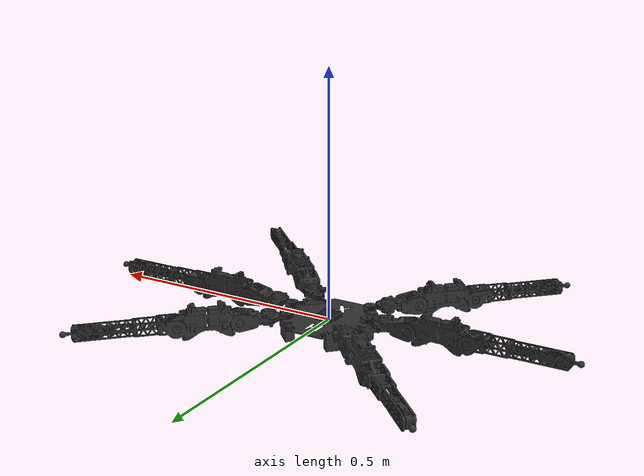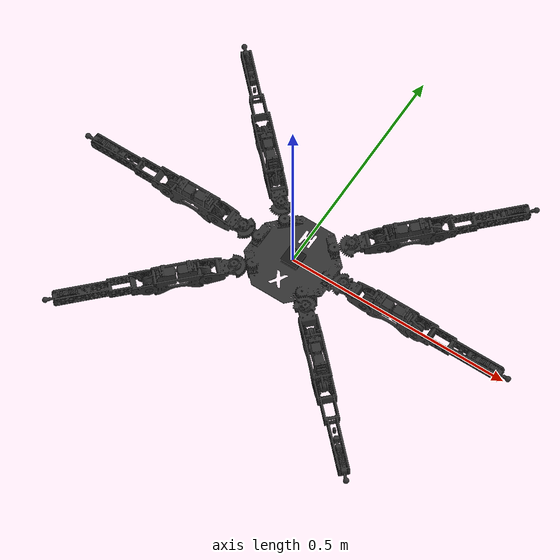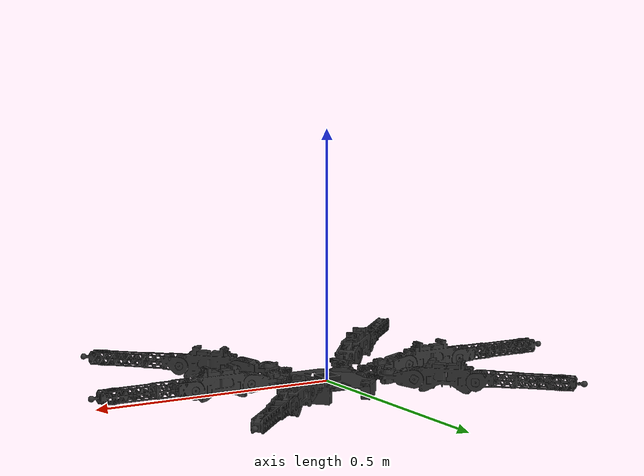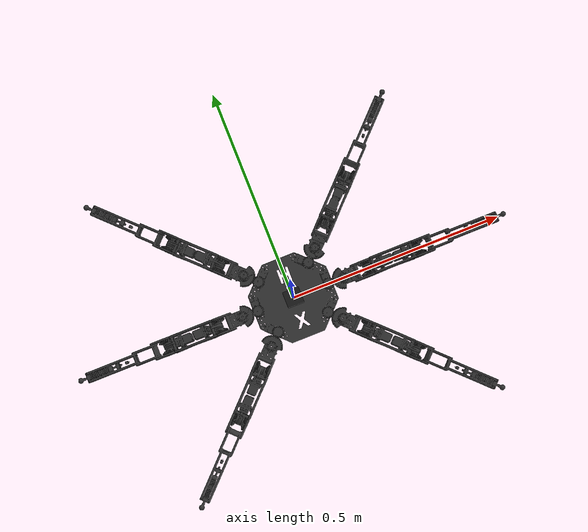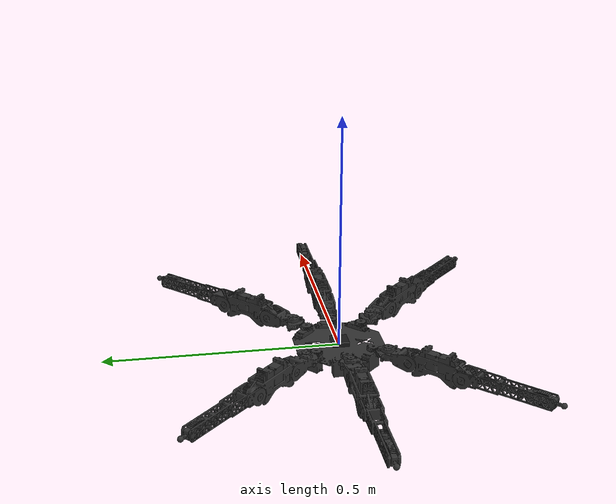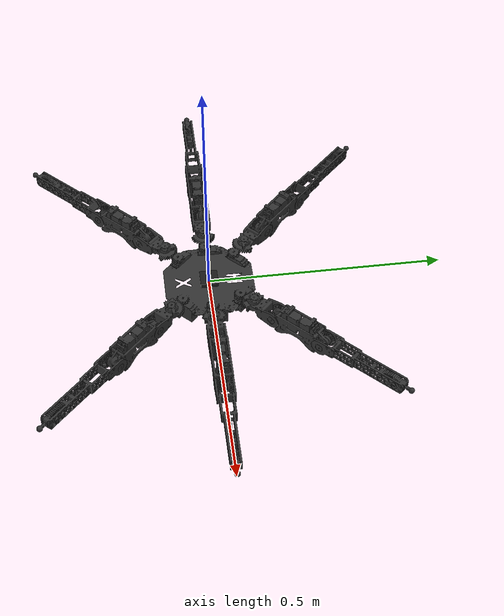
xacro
<?xml version="1.0"?>
<robot name="hexapod" xmlns:xacro="http://ros.org/wiki/xacro">
    <xacro:arg name="prefix" default="" />
    <xacro:arg name="use_gazebo" default="false" />
    <xacro:arg name="use_fake_hardware" default="false" />
    <xacro:arg name="fake_sensor_commands" default="false" />
    <xacro:arg name="port_name" default="/dev/ttyUSB0" />
    <xacro:arg name="baud_rate" default="115200" />
    <xacro:arg name="version" default="2" />

    <xacro:include filename="$(find hexapod_description)/urdf/hexapod_ee.urdf.xacro" />
    <xacro:hexapod_ee
        use_sim="true"
        prefix="$(arg prefix)"
        use_gazebo="$(arg use_gazebo)"
        use_fake_hardware="$(arg use_fake_hardware)"
        fake_sensor_commands="$(arg fake_sensor_commands)"
        port_name="$(arg port_name)"
        baud_rate="$(arg baud_rate)"
        version="$(arg version)" />
</robot>

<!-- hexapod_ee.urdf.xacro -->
<robot name="hexapod" xmlns:xacro="http://ros.org/wiki/xacro">
  <xacro:macro name="hexapod_ee" params="use_sim prefix use_gazebo use_fake_hardware fake_sensor_commands port_name baud_rate version">

    <xacro:include filename="$(find hexapod_description)/gazebo/hexapod.gazebo.xacro" />
    <xacro:include filename="$(find hexapod_description)/urdf/hexapod_leg_ee.urdf.xacro" />
    <xacro:include filename="$(find hexapod_description)/urdf/hexapod_gazebo.urdf.xacro" />
    <xacro:include filename="$(find hexapod_description)/urdf/imu.urdf.xacro"/>
    <xacro:include filename="$(find hexapod_moveit_config)/config/hexapod.ros2_control.xacro" />

    <xacro:hexapod_leg_ee prefix="${prefix}" version="${version}"/>
    <xacro:hexapod_gazebo prefix="${prefix}" />

    <xacro:imu_sensor
    prefix="${prefix}"
    parent="${prefix}base_link"
    frame_id="imu"
    xyz_offset="0 0 0.006"
    rpy_offset="0 0 0"
    update_rate="15.0"
    topic_name="imu/data"/>

    <gazebo>
      <plugin filename="gz_ros2_control-system" name="gz_ros2_control::GazeboSimROS2ControlPlugin">
        <parameters>$(find hex_gz)/config/gazebo_controller_manager.yaml</parameters>
      </plugin>
    </gazebo>

    <gazebo reference="imu">
      <sensor name="imu_sensor" type="imu">
        <update_rate>100.0</update_rate>
        <always_on>true</always_on>
        <visualize>true</visualize>
        <topic>imu/data</topic>
        <imu>
          <topic>imu/data</topic>
          <gaussian_noise>0.01</gaussian_noise>
          <bias_mean>0.0</bias_mean>
          <bias_stddev>0.0</bias_stddev>
        </imu>
      </sensor>
    </gazebo>

    <xacro:hexapod_ros2_control
        name="hexapod"
        initial_positions_file="$(find hexapod_description)/config/initial_positions.yaml"
        use_gazebo="${use_gazebo}"
        use_fake_hardware="${use_fake_hardware}"
        fake_sensor_commands="${fake_sensor_commands}"
        port_name="${port_name}"
        baud_rate="${baud_rate}" />
  </xacro:macro>
</robot>

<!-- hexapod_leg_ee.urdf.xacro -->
<robot xmlns:xacro="http://www.ros.org/wiki/xacro">
  <xacro:macro name="hexapod_leg_ee" params="prefix version">
    <xacro:if value="${int(version) == 1}">
      <!-- CECHY INERCJI -->
      <xacro:property name="platform_mass" value="0.3" />
      <xacro:property name="up_section_mass" value="0.1" />
      <xacro:property name="mid_section_mass" value="0.1" />
      <xacro:property name="down_section_mass" value="0.1" />
      <xacro:property name="ixx" value="0.001"/>
      <xacro:property name="iyy" value="0.001"/>
      <xacro:property name="izz" value="0.001"/>

      <!-- OGRANICZENIA KĄTOWE JOINTÓW -->
      <xacro:property name="joint1_lower" value="-0.5236"/>
      <xacro:property name="joint1_upper" value="0.5236"/>
      <xacro:property name="joint2_lower" value="-0.261799388"/>
      <xacro:property name="joint2_upper" value="1.308996939"/>
      <xacro:property name="joint3_lower" value="0"/>
      <xacro:property name="joint3_upper" value="1.570796327"/>

      <!-- CECHY POŁOŻENIA STAWÓW LEG 1 -->
      <xacro:property name="joint1_1_xyz" value="-0.063746 0.067285 0.003274"/>
      <xacro:property name="joint1_1_axis" value="0 0 1"/>

      <xacro:property name="joint2_1_xyz" value="-0.018864 0.024671 -0.020002"/>
      <xacro:property name="joint2_1_axis" value="-0.7968540982 -0.6041717854 0"/>

      <xacro:property name="joint3_1_xyz" value="-0.054636 0.071451 0.00505"/>
      <xacro:property name="joint3_1_axis" value="-0.7968540982 -0.6041717854 0"/>

      <xacro:property name="joint4_1_xyz" value="-0.099587 0.130461 -0.000046"/>
      <xacro:property name="joint4_1_axis" value="0 0 0"/>

      <!-- CECHY POŁOŻENIA LINKÓW LEG 1 -->
      <xacro:property name="link2_1_xyz" value="-0.013611 0.016988 -0.000419"/>
      <xacro:property name="link2_1_rpy" value="0 0 0.654498469"/>
      <xacro:property name="link3_1_xyz" value="-0.024936 0.032658 0.000547"/>
      <xacro:property name="link3_1_rpy" value="0 0 0.654498469"/>
      <xacro:property name="link4_1_xyz" value="-0.039176 0.05167 0"/>
      <xacro:property name="link4_1_rpy" value="0 0 0.654498469"/>

      <!-- CECHY POŁOŻENIA STAWÓW LEG 2 -->
      <xacro:property name="joint1_2_xyz" value="-0.005442 0.097816 0.003274"/>
      <xacro:property name="joint1_2_axis" value="0 0 1"/>

      <xacro:property name="joint2_2_xyz" value="0.0 0.031057 -0.020002"/>
      <xacro:property name="joint2_2_axis" value="-1 0 0"/>

      <xacro:property name="joint3_2_xyz" value="0.0 0.089946 0.00505"/>
      <xacro:property name="joint3_2_axis" value="-1 0 0"/>

      <xacro:property name="joint4_2_xyz" value="0.000147 0.164223 -0.000046"/>
      <xacro:property name="joint4_2_axis" value="0 0 0"/>

      <!-- CECHY POŁOŻENIA LINKÓW LEG 2 -->
      <xacro:property name="link2_2_xyz" value="-0.000493 0.021762 -0.000419"/>
      <xacro:property name="link2_2_rpy" value="0 0 0"/>
      <xacro:property name="link3_2_xyz" value="0.0 0.041 0.000546"/>
      <xacro:property name="link3_2_rpy" value="0 0 0"/>
      <xacro:property name="link4_2_xyz" value="0.000265 0.064842 0.0"/>
      <xacro:property name="link4_2_rpy" value="0 0 0"/>

      <!-- CECHY POŁOŻENIA STAWÓW LEG 3 -->
      <xacro:property name="joint1_3_xyz" value="0.055103 0.073938 0.003274"/>
      <xacro:property name="joint1_3_axis" value="0 0 1"/>

      <xacro:property name="joint2_3_xyz" value="0.018864 0.024671 -0.020002"/>
      <xacro:property name="joint2_3_axis" value="-0.794374 0.6074290528 0"/>

      <xacro:property name="joint3_3_xyz" value="0.054636 0.071451 0.00505"/>
      <xacro:property name="joint3_3_axis" value="-0.794374 0.6074290528 0"/>

      <xacro:property name="joint4_3_xyz" value="0.099252 0.130694 -0.000046"/>
      <xacro:property name="joint4_3_axis" value="0 0 0"/>

      <!-- CECHY POŁOŻENIA LINKÓW LEG 3 -->
      <xacro:property name="link2_3_xyz" value="0.012827 0.017587 -0.000419"/>
      <xacro:property name="link2_3_rpy" value="0 0 -0.654498469"/>
      <xacro:property name="link3_3_xyz" value="0.024936 0.032658 0.000547"/>
      <xacro:property name="link3_3_rpy" value="0 0 -0.654498469"/>
      <xacro:property name="link4_3_xyz" value="0.039176 0.05167 0"/>
      <xacro:property name="link4_3_rpy" value="0 0 -0.654498469"/>

      <!-- CECHY POŁOŻENIA STAWÓW LEG 4 -->
      <xacro:property name="joint1_4_xyz" value="0.055103 -0.073938 0.003274"/>
      <xacro:property name="joint1_4_axis" value="0 0 1"/>

      <xacro:property name="joint2_4_xyz" value="0.018864 -0.024671 -0.020002"/>
      <xacro:property name="joint2_4_axis" value="0.6074290528 0.794374 0"/>

      <xacro:property name="joint3_4_xyz" value="0.054636 -0.071451 0.00505"/>
      <xacro:property name="joint3_4_axis" value="0.794374 0.6074290528 0"/>

      <xacro:property name="joint4_4_xyz" value="0.099758 -0.130448 -0.000046"/>
      <xacro:property name="joint4_4_axis" value="0 0 0"/>

      <!-- CECHY POŁOŻENIA LINKÓW LEG 4 -->
      <xacro:property name="link2_4_xyz" value="0.013611 -0.016988 -0.000419"/>
      <xacro:property name="link2_4_rpy" value="0 0 3.796091123"/>
      <xacro:property name="link3_4_xyz" value="0.024936 -0.032658 0.000547"/>
      <xacro:property name="link3_4_rpy" value="0 0 3.796091123"/>
      <xacro:property name="link4_4_xyz" value="0.039176 -0.05167 0"/>
      <xacro:property name="link4_4_rpy" value="0 0 3.796091123"/>

      <!-- CECHY POŁOŻENIA STAWÓW LEG 5 -->
      <xacro:property name="joint1_5_xyz" value="-0.005442 -0.097816 0.003274"/>
      <xacro:property name="joint1_5_axis" value="0 0 1"/>

      <xacro:property name="joint2_5_xyz" value="0.0 -0.031057 -0.020002"/>
      <xacro:property name="joint2_5_axis" value="1 0 0"/>

      <xacro:property name="joint3_5_xyz" value="0.0 -0.089946 0.00505"/>
      <xacro:property name="joint3_5_axis" value="1 0 0"/>

      <xacro:property name="joint4_5_xyz" value="-0.000051 -0.164207 -0.000046"/>
      <xacro:property name="joint4_5_axis" value="0 0 0"/>

      <!-- CECHY POŁOŻENIA LINKÓW LEG 5 -->
      <xacro:property name="link2_5_xyz" value="0.000493 -0.021762 -0.000419"/>
      <xacro:property name="link2_5_rpy" value="0 0 3.141592654"/>
      <xacro:property name="link3_5_xyz" value="0.0 -0.041 0.000546"/>
      <xacro:property name="link3_5_rpy" value="0 0 3.141592654"/>
      <xacro:property name="link4_5_xyz" value="-0.000265 -0.064842 0.0"/>
      <xacro:property name="link4_5_rpy" value="0 0 3.141592654"/>

      <!-- CECHY POŁOŻENIA STAWÓW LEG 6 -->
      <xacro:property name="joint1_6_xyz" value="-0.063746 -0.067285 0.003274"/>
      <xacro:property name="joint1_6_axis" value="0 0 1"/>

      <xacro:property name="joint2_6_xyz" value="-0.018864 -0.024671 -0.020002"/>
      <xacro:property name="joint2_6_axis" value="0.794374 -0.6074290528 0"/>

      <xacro:property name="joint3_6_xyz" value="-0.054636 -0.071451 0.00505"/>
      <xacro:property name="joint3_6_axis" value="0.794374 -0.6074290528 0"/>

      <xacro:property name="joint4_6_xyz" value="-0.099223 -0.130739 -0.000046"/>
      <xacro:property name="joint4_6_axis" value="0 0 0"/>

      <!-- CECHY POŁOŻENIA LINKÓW LEG 6 -->
      <xacro:property name="link2_6_xyz" value="-0.012827 -0.017588 -0.000419"/>
      <xacro:property name="link2_6_rpy" value="0 0 2.487094184"/>
      <xacro:property name="link3_6_xyz" value="-0.024936 -0.032658 0.000547"/>
      <xacro:property name="link3_6_rpy" value="0 0 2.487094184"/>
      <xacro:property name="link4_6_xyz" value="-0.039176 -0.05167 0"/>
      <xacro:property name="link4_6_rpy" value="0 0 2.487094184"/>

    </xacro:if>

    <!-- DLA NOWEJ WERSJI HEXAPODA ZMIENIĆ PONIŻSZE PARAMETRY -->
    <xacro:if value="${int(version) == 2}">
      <!-- CECHY INERCJI -->
      <xacro:property name="platform_mass" value="0.4" />
      <xacro:property name="up_section_mass" value="0.12" />
      <xacro:property name="mid_section_mass" value="0.12" />
      <xacro:property name="down_section_mass" value="0.12" />
      <xacro:property name="ixx" value="0.002"/>
      <xacro:property name="iyy" value="0.002"/>
      <xacro:property name="izz" value="0.002"/>

      <!-- OGRANICZENIA KĄTOWE JOINTÓW -->
      <xacro:property name="joint1_lower" value="-0.785398163"/>
      <xacro:property name="joint1_upper" value="0.785398163"/>
      <xacro:property name="joint2_lower" value="-1.047197551"/>
      <xacro:property name="joint2_upper" value="1.047197551"/>
      <xacro:property name="joint3_lower" value="-0.523598776"/>
      <xacro:property name="joint3_upper" value="1.570796327"/>

      <!-- CECHY POŁOŻENIA STAWÓW LEG 1 -->
      <xacro:property name="joint1_1_xyz" value="0.086185	0.0860902	0.0170504"/>
      <xacro:property name="joint1_1_axis" value="0	0	1"/>

      <xacro:property name="joint2_1_xyz" value="0.041059	0.0410588	0.0002496"/>
      <xacro:property name="joint2_1_axis" value="-0.707106781	0.707106781	0"/>

      <xacro:property name="joint3_1_xyz" value="0.085418	0.085419	0"/>
      <xacro:property name="joint3_1_axis" value="-0.707106781	0.707106781	0"/>

      <xacro:property name="joint4_1_xyz" value="0.147786	0.147786	0.0048551"/>
      <xacro:property name="joint4_1_axis" value="0	0	0"/>

      <!-- CECHY POŁOŻENIA LINKÓW LEG 1 -->
      <xacro:property name="link2_1_xyz" value="0.003017	0.0026184	-0.0000519"/>
      <xacro:property name="link2_1_rpy" value="0	0	0.7853981634"/>
      <xacro:property name="link3_1_xyz" value="0.039867	0.039421	0.00014"/>
      <xacro:property name="link3_1_rpy" value="0	0	0.7853981634"/>
      <xacro:property name="link4_1_xyz" value="0.082477	0.082555	0.0045585"/>
      <xacro:property name="link4_1_rpy" value="0	0	0.7853981634"/>
      <xacro:property name="link5_1_xyz" value="0	0	0"/>
      <xacro:property name="link_tip_1_rpy" value="0 0 0.785398163"/>

      <!-- CECHY POŁOŻENIA STAWÓW LEG 2 -->
      <xacro:property name="joint1_2_xyz" value="0.121845	0	0.0170504"/>
      <xacro:property name="joint1_2_axis" value="0	0	1"/>

      <xacro:property name="joint2_2_xyz" value="0.058105	-0.000094711	0.0002496"/>
      <xacro:property name="joint2_2_axis" value="0	1	0"/>

      <xacro:property name="joint3_2_xyz" value="0.120802	0.000000002	0"/>
      <xacro:property name="joint3_2_axis" value="0	1	0"/>

      <xacro:property name="joint4_2_xyz" value="0.209002	-0.000000003	0.0048551"/>
      <xacro:property name="joint4_2_axis" value="0	0	0"/>

      <!-- CECHY POŁOŻENIA LINKÓW LEG 2 -->
      <xacro:property name="link2_2_xyz" value="0.003944	-0.000340488	-0.0000519"/>
      <xacro:property name="link2_2_rpy" value="0	0	0"/>
      <xacro:property name="link3_2_xyz" value="0.055988	-0.000035124	0.0001789"/>
      <xacro:property name="link3_2_rpy" value="0	0	0"/>
      <xacro:property name="link4_2_xyz" value="0.116837	0.000195559	0.0045585"/>
      <xacro:property name="link4_2_rpy" value="0	0	0"/>
      <xacro:property name="link5_2_xyz" value="0	0	0"/>
      <xacro:property name="link5_2_rpy" value="0	0	0"/>
      <xacro:property name="link_tip_2_rpy" value="0 0 0"/>

      <!-- CECHY POŁOŻENIA STAWÓW LEG 3 -->
      <xacro:property name="joint1_3_xyz" value="0.0861847	-0.0860902	0.0170504"/>
      <xacro:property name="joint1_3_axis" value="0	0	1"/>

      <xacro:property name="joint2_3_xyz" value="0.0410583	-0.0412488	0.0002496"/>
      <xacro:property name="joint2_3_axis" value="0.707106781	0.707106781	0"/>

      <xacro:property name="joint3_3_xyz" value="0.08542	-0.085418	0"/>
      <xacro:property name="joint3_3_axis" value="0.707106781	0.707106781	0"/>

      <xacro:property name="joint4_3_xyz" value="0.147785	-0.147785	0.0048551"/>
      <xacro:property name="joint4_3_axis" value="0	0	0"/>

      <!-- CECHY POŁOŻENIA LINKÓW LEG 3 -->
      <xacro:property name="link2_3_xyz" value="0.0029399	-0.002591	-0.0000519"/>
      <xacro:property name="link2_3_rpy" value="0	0	5.497787144"/>
      <xacro:property name="link3_3_xyz" value="0.03928	-0.039511	0.00014"/>
      <xacro:property name="link3_3_rpy" value="0	0	5.497787144"/>
      <xacro:property name="link4_3_xyz" value="0.082476	-0.082624	0.0045585"/>
      <xacro:property name="link4_3_rpy" value="0	0	5.497787144"/>
      <xacro:property name="link5_3_xyz" value="0	0	0"/>
      <xacro:property name="link5_3_rpy" value="0	0	0"/>
      <xacro:property name="link_tip_3_rpy" value="0 0 5.497787144"/>

      <!-- CECHY POŁOŻENIA STAWÓW LEG 4 -->
      <xacro:property name="joint1_4_xyz" value="-0.0861847	-0.0860902	0.0170504"/>
      <xacro:property name="joint1_4_axis" value="0	0	1"/>

      <xacro:property name="joint2_4_xyz" value="-0.0410583	-0.0412488	0.0002496"/>
      <xacro:property name="joint2_4_axis" value="0.707106781	-0.707106781	0"/>

      <xacro:property name="joint3_4_xyz" value="-0.08542	-0.085418	0"/>
      <xacro:property name="joint3_4_axis" value="0.707106781	-0.707106781	0"/>

      <xacro:property name="joint4_4_xyz" value="-0.147785	-0.147785	0.0048551"/>
      <xacro:property name="joint4_4_axis" value="0	0	0"/>

      <!-- CECHY POŁOŻENIA LINKÓW LEG 4 -->
      <xacro:property name="link2_4_xyz" value="-0.0029399	-0.002591	-0.0000519"/>
      <xacro:property name="link2_4_rpy" value="0	0	3.926990817"/>
      <xacro:property name="link3_4_xyz" value="-0.03928	-0.039511	0.00014"/>
      <xacro:property name="link3_4_rpy" value="0	0	3.926990817"/>
      <xacro:property name="link4_4_xyz" value="-0.082476	-0.082624	0.0045585"/>
      <xacro:property name="link4_4_rpy" value="0	0	3.926990817"/>
      <xacro:property name="link5_4_xyz" value="0	0	0"/>
      <xacro:property name="link5_4_rpy" value="0	0	0"/>
      <xacro:property name="link_tip_4_rpy" value="0 0 3.926990817"/>

      <!-- CECHY POŁOŻENIA STAWÓW LEG 5 -->
      <xacro:property name="joint1_5_xyz" value="-0.121845	0	0.0170504"/>
      <xacro:property name="joint1_5_axis" value="0	0	1"/>

      <xacro:property name="joint2_5_xyz" value="-0.058105	-0.000094711	0.0002496"/>
      <xacro:property name="joint2_5_axis" value="0	-1	0"/>

      <xacro:property name="joint3_5_xyz" value="-0.120802	0.000000002	0"/>
      <xacro:property name="joint3_5_axis" value="0	-1	0"/>

      <xacro:property name="joint4_5_xyz" value="-0.209002	-0.000000003	0.0048551"/>
      <xacro:property name="joint4_5_axis" value="0	0	0"/>

      <!-- CECHY POŁOŻENIA LINKÓW LEG 5 -->
      <xacro:property name="link2_5_xyz" value="-0.003953	-0.000340488	-0.0000519"/>
      <xacro:property name="link2_5_rpy" value="0	0	3.141592654"/>
      <xacro:property name="link3_5_xyz" value="-0.055988	-0.000035124	0.0001789"/>
      <xacro:property name="link3_5_rpy" value="0	0	3.141592654"/>
      <xacro:property name="link4_5_xyz" value="-0.116837	0.000195559	0.0045585"/>
      <xacro:property name="link4_5_rpy" value="0	0	3.141592654"/>
      <xacro:property name="link5_5_xyz" value="0	0	0"/>
      <xacro:property name="link5_5_rpy" value="0	0	0"/>
      <xacro:property name="link_tip_5_rpy" value="0 0 3.141592654"/>

      <!-- CECHY POŁOŻENIA STAWÓW LEG 6 -->
      <xacro:property name="joint1_6_xyz" value="-0.0859957	0.0860903	0.0170505"/>
      <xacro:property name="joint1_6_axis" value="0	0	1"/>

      <xacro:property name="joint2_6_xyz" value="-0.0412483	0.0410587	0.0002494"/>
      <xacro:property name="joint2_6_axis" value="-0.707106781	-0.707106781	0"/>

      <xacro:property name="joint3_6_xyz" value="-0.08542	0.085419	0.0000001"/>
      <xacro:property name="joint3_6_axis" value="-0.707106781	-0.707106781	0"/>

      <xacro:property name="joint4_6_xyz" value="-0.147786	0.147785	0.0048551"/>
      <xacro:property name="joint4_6_axis" value="0	0	0"/>

      <!-- CECHY POŁOŻENIA LINKÓW LEG 6 -->
      <xacro:property name="link2_6_xyz" value="-0.0029399	0.002591	-0.0000519"/>
      <xacro:property name="link2_6_rpy" value="0	0	2.35619449"/>
      <xacro:property name="link3_6_xyz" value="-0.03928	0.039511	0.00014"/>
      <xacro:property name="link3_6_rpy" value="0	0	2.364921136"/>
      <xacro:property name="link4_6_xyz" value="-0.082476	0.082624	0.0045585"/>
      <xacro:property name="link4_6_rpy" value="0	0	2.35619449"/>
      <xacro:property name="link5_6_xyz" value="0	0	0"/>
      <xacro:property name="link5_6_rpy" value="0	0	0"/>
      <xacro:property name="link_tip_6_rpy" value="0 0 2.35619449"/>

    </xacro:if>

    <xacro:property
        name="meshes_file_direction"
        value="package://hexapod_description/meshes/Version${version}"/>

    <!-- Include macro modeli kolizyjnych z prostych kształtów geometrycznych -->
     <xacro:if value="${int(version) == 1}">
      <xacro:include filename="$(find hexapod_description)/collision/Version1/platform_hitbox.xacro"/>
      <xacro:include filename="$(find hexapod_description)/collision/Version1/up_section_hitbox.xacro"/>
      <xacro:include filename="$(find hexapod_description)/collision/Version1/mid_section_hitbox.xacro"/>
      <xacro:include filename="$(find hexapod_description)/collision/Version1/down_section_hitbox.xacro"/>
    </xacro:if>

    <!-- NA RAZIE BRAK PROSTYCH MODELI KOLIZJI -->
    <xacro:if value="${int(version) == 2}">
       <xacro:include filename="$(find hexapod_description)/collision/Version2/platform_hitbox.xacro"/>
      <xacro:include filename="$(find hexapod_description)/collision/Version2/up_section_hitbox.xacro"/>
      <xacro:include filename="$(find hexapod_description)/collision/Version2/mid_section_hitbox.xacro"/>
      <xacro:include filename="$(find hexapod_description)/collision/Version2/down_section_hitbox.xacro"/>
      <xacro:include filename="$(find hexapod_description)/collision/Version2/tip_hitbox.xacro"/>
    </xacro:if>

    <!-- Macro platformy -->
      <xacro:macro name="platform_base" params="prefix">
        <link name="${prefix}base_link">
          <visual>
            <origin xyz="0 0 0" rpy="0 0 0"/>
            <geometry>
              <mesh filename="${meshes_file_direction}/platform.stl" scale="1 1 1"/>
            </geometry>
            <material name="gray">
              <color rgba="0.2 0.2 0.2 1"/>
            </material>
          </visual>

          <!-- MODEL KOLIZYJNY -->
          <xacro:platform_collision prefix="${prefix}" />
          <inertial>
            <origin xyz="0 0 0" rpy="0 0 0"/>
            <mass value="${platform_mass}"/>
            <inertia
              ixx="${ixx}" ixy="0.0" ixz="0.0"
              iyy="${iyy}" iyz="0.0"
              izz="${izz}"/>
          </inertial>
        </link>
      </xacro:macro>

    <!-- Macro: Joint -->
    <xacro:macro name="leg_joint" params="prefix joint_name parent_link child_link xyz axis lower upper">
      <joint name="${joint_name}" type="revolute">
        <parent link="${parent_link}"/>
        <child link="${child_link}"/>
        <origin xyz="${xyz}" rpy="0 0 0"/>
        <axis xyz="${axis}"/>
        <limit effort="5.0" velocity="1.0" lower="${lower}" upper="${upper}"/>
        <dynamics damping="0.1"/>
      </joint>
    </xacro:macro>

    <!-- Macro: UP_SECTION -->
    <xacro:macro name="upper_leg" params="prefix index xyz rpy">
      <link name="${prefix}link2_${index}">
        <visual>
          <origin xyz="${xyz}" rpy="${rpy}"/>
          <geometry>
            <mesh filename="${meshes_file_direction}/leg_up.stl" scale="1.0 1.0 1.0"/>
          </geometry>
          <material name="grey">
            <color rgba="0.2 0.2 0.2 1"/>
          </material>
        </visual>

        <!-- MODEL KOLIZYJNY -->
            <xacro:upper_leg_collision prefix="${prefix}" position="${xyz}" rotation="${rpy}"/>
        <inertial>
          <origin xyz="${xyz}" rpy="0.0 0.0 0.0"/>
          <mass value="${up_section_mass}"/>
          <inertia ixx="${ixx}" ixy="0.0" ixz="0.0" iyy="${iyy}" iyz="0.0" izz="${izz}"/>
        </inertial>
      </link>
    </xacro:macro>

    <!-- Macro: MID_SECTION -->
    <xacro:macro name="mid_leg" params="prefix index xyz rpy">
      <link name="${prefix}link3_${index}">
        <visual>
          <origin xyz="${xyz}" rpy="${rpy}"/>
          <geometry>
            <mesh filename="${meshes_file_direction}/leg_mid.stl" scale="1.0 1.0 1.0"/>
          </geometry>
          <material name="grey">
            <color rgba="0.2 0.2 0.2 1"/>
          </material>
        </visual>
            <xacro:mid_leg_collision prefix="${prefix}" position="${xyz}" rotation="${rpy}"/>
        <inertial>
          <origin xyz="${xyz}" rpy="${rpy}"/>
          <mass value="${mid_section_mass}"/>
          <inertia ixx="${ixx}" ixy="0.0" ixz="0.0" iyy="${iyy}" iyz="0.0" izz="${izz}"/>
        </inertial>
      </link>
    </xacro:macro>

    <!-- Macro: DOWN_SECTION -->
    <xacro:macro name="lower_leg" params="prefix index xyz rpy">
      <link name="${prefix}link4_${index}">
        <visual>
          <origin xyz="${xyz}" rpy="${rpy}"/>
          <geometry>
            <mesh filename="${meshes_file_direction}/leg_down.stl" scale="1.0 1.0 1.0"/>
          </geometry>
          <material name="grey">
            <color rgba="0.2 0.2 0.2 1"/>
          </material>
        </visual>
            <xacro:lower_leg_collision prefix="${prefix}" position="${xyz}" rotation="${rpy}"/>
        <inertial>
          <origin xyz="${xyz}" rpy="${rpy}"/>
          <mass value="${down_section_mass}"/>
          <inertia ixx="${ixx}" ixy="0.0" ixz="0.0" iyy="${iyy}" iyz="0.0" izz="${izz}"/>
        </inertial>
      </link>
    </xacro:macro>

  <!-- Macro: Effector Joint -->
  <xacro:macro name="end_effector_joint" params="prefix index xyz rpy">
    <joint name="${prefix}joint4_${index}" type="fixed">
      <parent link="${prefix}link4_${index}"/>
      <child link="${prefix}link5_${index}"/>
      <origin xyz="${xyz}" rpy="${rpy}"/>
    </joint>
  </xacro:macro>

  <!-- Macro: Effector -->
   <xacro:if value="${int(version) == 1}">
      <xacro:macro name="end_effector_link" params="prefix index">
        <link name="${prefix}link5_${index}"/>
      </xacro:macro>
   </xacro:if>

  <xacro:if value="${int(version) == 2}">
    <xacro:macro name="end_effector_link" params="prefix index rpy">
      <link name="${prefix}link5_${index}">
        <xacro:tip_collision prefix="${prefix}" rotation="${rpy}"/>
        <inertial>
        <origin xyz="0 0 0" rpy="0 0 0"/>
        <mass value="0.05"/>  <!-- Mała masa dla end effector -->
        <inertia
          ixx="0.0001" ixy="0.0" ixz="0.0"
          iyy="0.0001" iyz="0.0"
          izz="0.0001"/>
      </inertial>
      <visual>
        <origin xyz="0 0 0" rpy="0 0 0"/>
        <geometry>
          <sphere radius="0.005"/>
        </geometry>
        <material name="grey">
          <color rgba="0.2 0.2 0.2 1"/>
        </material>
      </visual>
      </link>
    </xacro:macro>
  </xacro:if>

  <xacro:macro name="hexapod" params="prefix version">
      <!-- Platform -->
    <xacro:platform_base prefix="${prefix}" />

    <!-- LEG 1 - używa zmiennych zamiast wartości na twardo -->
    <xacro:leg_joint
      prefix="${prefix}"
      joint_name="${prefix}joint1_1"
      parent_link="${prefix}base_link"
      child_link="${prefix}link2_1"
      xyz="${joint1_1_xyz}"
      axis="${joint1_1_axis}"
      lower="${joint1_lower}"
      upper="${joint1_upper}" />
    <xacro:upper_leg prefix="${prefix}" index="1" xyz="${link2_1_xyz}" rpy="${link2_1_rpy}" />

    <xacro:leg_joint
      prefix="${prefix}"
      joint_name="${prefix}joint2_1"
      parent_link="${prefix}link2_1"
      child_link="${prefix}link3_1"
      xyz="${joint2_1_xyz}"
      axis="${joint2_1_axis}"
      lower="${joint2_lower}"
      upper="${joint2_upper}" />
    <xacro:mid_leg prefix="${prefix}" index="1" xyz="${link3_1_xyz}" rpy="${link3_1_rpy}" />

    <xacro:leg_joint
      prefix="${prefix}"
      joint_name="${prefix}joint3_1"
      parent_link="${prefix}link3_1"
      child_link="${prefix}link4_1"
      xyz="${joint3_1_xyz}"
      axis="${joint3_1_axis}"
      lower="${joint3_lower}"
      upper="${joint3_upper}" />
    <xacro:lower_leg prefix="${prefix}" index="1" xyz="${link4_1_xyz}" rpy="${link4_1_rpy}" />

    <xacro:end_effector_joint prefix="${prefix}" index="1" xyz="${joint4_1_xyz}" rpy="${joint4_1_axis}"/>
    <xacro:if value="${int(version) == 1}">
      <xacro:end_effector_link prefix="${prefix}" index="1"/>
    </xacro:if>
    <xacro:if value="${int(version) == 2}">
      <xacro:end_effector_link prefix="${prefix}" index="1" rpy="${link_tip_1_rpy}"/>
    </xacro:if>

    <!-- LEG 2 - używa zmiennych zamiast wartości na twardo -->
    <xacro:leg_joint
      prefix="${prefix}"
      joint_name="${prefix}joint1_2"
      parent_link="${prefix}base_link"
      child_link="${prefix}link2_2"
      xyz="${joint1_2_xyz}"
      axis="${joint1_2_axis}"
      lower="${joint1_lower}"
      upper="${joint1_upper}"/>
    <xacro:upper_leg prefix="${prefix}" index="2" xyz="${link2_2_xyz}" rpy="${link2_2_rpy}"/>

    <xacro:leg_joint
      prefix="${prefix}"
      joint_name="${prefix}joint2_2"
      parent_link="${prefix}link2_2"
      child_link="${prefix}link3_2"
      xyz="${joint2_2_xyz}"
      axis="${joint2_2_axis}"
      lower="${joint2_lower}"
      upper="${joint2_upper}"/>
    <xacro:mid_leg prefix="${prefix}" index="2" xyz="${link3_2_xyz}" rpy="${link3_2_rpy}"/>

    <xacro:leg_joint
      prefix="${prefix}"
      joint_name="${prefix}joint3_2"
      parent_link="${prefix}link3_2"
      child_link="${prefix}link4_2"
      xyz="${joint3_2_xyz}"
      axis="${joint3_2_axis}"
      lower="${joint3_lower}"
      upper="${joint3_upper}"/>
    <xacro:lower_leg prefix="${prefix}" index="2" xyz="${link4_2_xyz}" rpy="${link4_2_rpy}"/>

    <xacro:end_effector_joint prefix="${prefix}" index="2" xyz="${joint4_2_xyz}" rpy="${joint4_2_axis}"/>
    <xacro:if value="${int(version) == 1}">
      <xacro:end_effector_link prefix="${prefix}" index="2"/>
    </xacro:if>
    <xacro:if value="${int(version) == 2}">
      <xacro:end_effector_link prefix="${prefix}" index="2" rpy="${link_tip_2_rpy}"/>
    </xacro:if>

    <!-- LEG 3 - używa zmiennych zamiast wartości na twardo -->
    <xacro:leg_joint
      prefix="${prefix}"
      joint_name="${prefix}joint1_3"
      parent_link="${prefix}base_link"
      child_link="${prefix}link2_3"
      xyz="${joint1_3_xyz}"
      axis="${joint1_3_axis}"
      lower="${joint1_lower}"
      upper="${joint1_upper}"/>
    <xacro:upper_leg prefix="${prefix}" index="3" xyz="${link2_3_xyz}" rpy="${link2_3_rpy}"/>

    <xacro:leg_joint
      prefix="${prefix}"
      joint_name="${prefix}joint2_3"
      parent_link="${prefix}link2_3"
      child_link="${prefix}link3_3"
      xyz="${joint2_3_xyz}"
      axis="${joint2_3_axis}"
      lower="${joint2_lower}"
      upper="${joint2_upper}"/>
    <xacro:mid_leg prefix="${prefix}" index="3" xyz="${link3_3_xyz}" rpy="${link3_3_rpy}"/>

    <xacro:leg_joint
      prefix="${prefix}"
      joint_name="${prefix}joint3_3"
      parent_link="${prefix}link3_3"
      child_link="${prefix}link4_3"
      xyz="${joint3_3_xyz}"
      axis="${joint3_3_axis}"
      lower="${joint3_lower}"
      upper="${joint3_upper}"/>
    <xacro:lower_leg prefix="${prefix}" index="3" xyz="${link4_3_xyz}" rpy="${link4_3_rpy}"/>

    <xacro:end_effector_joint prefix="${prefix}" index="3" xyz="${joint4_3_xyz}" rpy="${joint4_3_axis}"/>
    <xacro:if value="${int(version) == 1}">
      <xacro:end_effector_link prefix="${prefix}" index="3"/>
    </xacro:if>
    <xacro:if value="${int(version) == 2}">
      <xacro:end_effector_link prefix="${prefix}" index="3" rpy="${link_tip_3_rpy}"/>
    </xacro:if>

    <!-- LEG 4 - używa zmiennych zamiast wartości na twardo -->
    <xacro:leg_joint
      prefix="${prefix}"
      joint_name="${prefix}joint1_4"
      parent_link="${prefix}base_link"
      child_link="${prefix}link2_4"
      xyz="${joint1_4_xyz}"
      axis="${joint1_4_axis}"
      lower="${joint1_lower}"
      upper="${joint1_upper}"/>
    <xacro:upper_leg prefix="${prefix}" index="4" xyz="${link2_4_xyz}" rpy="${link2_4_rpy}"/>

    <xacro:leg_joint
      prefix="${prefix}"
      joint_name="${prefix}joint2_4"
      parent_link="${prefix}link2_4"
      child_link="${prefix}link3_4"
      xyz="${joint2_4_xyz}"
      axis="${joint2_4_axis}"
      lower="${joint2_lower}"
      upper="${joint2_upper}"/>
    <xacro:mid_leg prefix="${prefix}" index="4" xyz="${link3_4_xyz}" rpy="${link3_4_rpy}"/>

    <xacro:leg_joint
      prefix="${prefix}"
      joint_name="${prefix}joint3_4"
      parent_link="${prefix}link3_4"
      child_link="${prefix}link4_4"
      xyz="${joint3_4_xyz}"
      axis="${joint3_4_axis}"
      lower="${joint3_lower}"
      upper="${joint3_upper}"/>
    <xacro:lower_leg prefix="${prefix}" index="4" xyz="${link4_4_xyz}" rpy="${link4_4_rpy}"/>

    <xacro:end_effector_joint prefix="${prefix}" index="4" xyz="${joint4_4_xyz}" rpy="${joint4_4_axis}"/>
    <xacro:if value="${int(version) == 1}">
      <xacro:end_effector_link prefix="${prefix}" index="4"/>
    </xacro:if>
    <xacro:if value="${int(version) == 2}">
      <xacro:end_effector_link prefix="${prefix}" index="4" rpy="${link_tip_4_rpy}"/>
    </xacro:if>

    <!-- LEG 5 - używa zmiennych zamiast wartości na twardo -->
    <xacro:leg_joint
      prefix="${prefix}"
      joint_name="${prefix}joint1_5"
      parent_link="${prefix}base_link"
      child_link="${prefix}link2_5"
      xyz="${joint1_5_xyz}"
      axis="${joint1_5_axis}"
      lower="${joint1_lower}"
      upper="${joint1_upper}"/>
    <xacro:upper_leg prefix="${prefix}" index="5" xyz="${link2_5_xyz}" rpy="${link2_5_rpy}"/>

    <xacro:leg_joint
      prefix="${prefix}"
      joint_name="${prefix}joint2_5"
      parent_link="${prefix}link2_5"
      child_link="${prefix}link3_5"
      xyz="${joint2_5_xyz}"
      axis="${joint2_5_axis}"
      lower="${joint2_lower}"
      upper="${joint2_upper}"/>
    <xacro:mid_leg prefix="${prefix}" index="5" xyz="${link3_5_xyz}" rpy="${link3_5_rpy}"/>

    <xacro:leg_joint
      prefix="${prefix}"
      joint_name="${prefix}joint3_5"
      parent_link="${prefix}link3_5"
      child_link="${prefix}link4_5"
      xyz="${joint3_5_xyz}"
      axis="${joint3_5_axis}"
      lower="${joint3_lower}"
      upper="${joint3_upper}"/>
    <xacro:lower_leg prefix="${prefix}" index="5" xyz="${link4_5_xyz}" rpy="${link4_5_rpy}"/>

    <xacro:end_effector_joint prefix="${prefix}" index="5" xyz="${joint4_5_xyz}" rpy="${joint4_5_axis}"/>
    <xacro:if value="${int(version) == 1}">
      <xacro:end_effector_link prefix="${prefix}" index="5"/>
    </xacro:if>
    <xacro:if value="${int(version) == 2}">
      <xacro:end_effector_link prefix="${prefix}" index="5" rpy="${link_tip_5_rpy}"/>
    </xacro:if>

    <!-- LEG 6 - używa zmiennych zamiast wartości na twardo -->
    <xacro:leg_joint
      prefix="${prefix}"
      joint_name="${prefix}joint1_6"
      parent_link="${prefix}base_link"
      child_link="${prefix}link2_6"
      xyz="${joint1_6_xyz}"
      axis="${joint1_6_axis}"
      lower="${joint1_lower}"
      upper="${joint1_upper}"/>
    <xacro:upper_leg prefix="${prefix}" index="6" xyz="${link2_6_xyz}" rpy="${link2_6_rpy}"/>

    <xacro:leg_joint
      prefix="${prefix}"
      joint_name="${prefix}joint2_6"
      parent_link="${prefix}link2_6"
      child_link="${prefix}link3_6"
      xyz="${joint2_6_xyz}"
      axis="${joint2_6_axis}"
      lower="${joint2_lower}"
      upper="${joint2_upper}"/>
    <xacro:mid_leg prefix="${prefix}" index="6" xyz="${link3_6_xyz}" rpy="${link3_6_rpy}"/>

    <xacro:leg_joint
      prefix="${prefix}"
      joint_name="${prefix}joint3_6"
      parent_link="${prefix}link3_6"
      child_link="${prefix}link4_6"
      xyz="${joint3_6_xyz}"
      axis="${joint3_6_axis}"
      lower="${joint3_lower}"
      upper="${joint3_upper}"/>
    <xacro:lower_leg prefix="${prefix}" index="6" xyz="${link4_6_xyz}" rpy="${link4_6_rpy}"/>

    <xacro:end_effector_joint prefix="${prefix}" index="6" xyz="${joint4_6_xyz}" rpy="${joint4_6_axis}"/>
    <xacro:if value="${int(version) == 1}">
      <xacro:end_effector_link prefix="${prefix}" index="6"/>
    </xacro:if>
    <xacro:if value="${int(version) == 2}">
      <xacro:end_effector_link prefix="${prefix}" index="6" rpy="${link_tip_6_rpy}"/>
    </xacro:if>

  </xacro:macro>

  <!-- Macro wywołujące hexapoda -->
  <xacro:hexapod prefix="${prefix}" version="${version}"/>

</xacro:macro>

</robot>

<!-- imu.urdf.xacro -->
<robot xmlns:xacro="http://www.ros.org/wiki/xacro">
    <xacro:property name="M_PI" value="3.1415926535897931" />
    <xacro:arg name="prefix" default=""/>
    <!-- imu jest ale nie wysyla nic -> do naprawy :( -->

    <xacro:macro name="imu_sensor" params="
        prefix:=''
        parent:='$(arg prefix)base_link'
        frame_id:='imu'
        xyz_offset:='0 0 0'
        rpy_offset:='0 0 0'
        inertial_xyz_offset:='0 0 0'
        inertial_rpy_offset:='0 0 0'
        mass:=0.031
        length:=0.03899
        width:=0.03785
        height:=0.01338
        material_name:='imu_black'
        material_color:='0.1 0.1 0.1 1'
        gazebo_material_ambient:='0.1 0.1 0.1 1'
        gazebo_material_diffuse:='0.1 0.1 0.1 1'
        gazebo_material_specular:='0.1 0.1 0.1 1'
        update_rate:='15.0'
        topic_name:='imu/data'
        always_on:=true
        visualize:=false">

        <xacro:property name="ixx" value="${(mass/12.0) * (height*height + width*width)}" />
        <xacro:property name="iyy" value="${(mass/12.0) * (length*length + height*height)}" />
        <xacro:property name="izz" value="${(mass/12.0) * (length*length + width*width)}" />

        <link name="${prefix}${frame_id}_link">
            <visual>
                <origin xyz="0 0 0" rpy="0 0 0"/>
                <geometry>
                    <box size="${length} ${width} ${height}"/>
                </geometry>
                <material name="${material_name}">
                    <color rgba="${material_color}"/>
                </material>
            </visual>

            <inertial>
                <mass value="${mass}" />
                <origin xyz="${inertial_xyz_offset}" rpy="${inertial_rpy_offset}"/>
                <inertia
                    ixx="${ixx}"
                    ixy="0.0"
                    ixz="0.0"
                    iyy="${iyy}"
                    iyz="0.0"
                    izz="${izz}" />
            </inertial>
        </link>

        <joint name="${prefix}${frame_id}_joint" type="fixed">
            <parent link="${prefix}${parent}"/>
            <child link="${prefix}${frame_id}_link" />
            <origin xyz="${xyz_offset}" rpy="${rpy_offset}"/>
        </joint>

        <gazebo reference="${prefix}${frame_id}_link">
            <material>
                <ambient>${gazebo_material_ambient}</ambient>
                <diffuse>${gazebo_material_diffuse}</diffuse>
                <specular>${gazebo_material_specular}</specular>
            </material>
            <sensor name="${prefix}imu_sensor" type="imu">
                <topic>${topic_name}</topic>
                <update_rate>${update_rate}</update_rate>
                <always_on>${always_on}</always_on>
                <visualize>${visualize}</visualize>
                <gz_frame_id>${prefix}${frame_id}_link</gz_frame_id>
            </sensor>
        </gazebo>
    </xacro:macro>
</robot>

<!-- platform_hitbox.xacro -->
<robot xmlns:xacro="http://www.ros.org/wiki/xacro">
    <!-- Macro modelu kolizji platformy V2 złożonego z sześcianów i cylindrów -->
<xacro:macro name="platform_collision" params="prefix">
    <!-- Sześcian 0 -->
    <collision>
      <origin xyz="0 0 0.00210" rpy="0 0 0"/>
      <geometry>
        <box size="0.19000 0.07820 0.00320"/>
      </geometry>
    </collision>

    <!-- Sześcian 1 -->
    <collision>
      <origin xyz="0.04104 0.04082 0.00210" rpy="0 0 0.78540"/>
      <geometry>
        <box size="0.07320 0.08000 0.00320"/>
      </geometry>
    </collision>

    <!-- Sześcian 2 -->
    <collision>
      <origin xyz="0.04104 -0.04082 0.00210" rpy="0 0 -0.78540"/>
      <geometry>
        <box size="0.07320 0.08000 0.00320"/>
      </geometry>
    </collision>

    <!-- Sześcian 3 -->
    <collision>
      <origin xyz="-0.04104 0.04082 0.00210" rpy="0 0 -0.78540"/>
      <geometry>
        <box size="0.07320 0.08000 0.00320"/>
      </geometry>
    </collision>

    <!-- Sześcian 4 -->
    <collision>
      <origin xyz="-0.04104 -0.04082 0.00210" rpy="0 0 0.78540"/>
      <geometry>
        <box size="0.07320 0.08000 0.00320"/>
      </geometry>
    </collision>

    <!-- Sześcian 5 -->
    <collision>
      <origin xyz="0 0 0.00210" rpy="0 0 0"/>
      <geometry>
        <box size="0.07820 0.19000 0.00320"/>
      </geometry>
    </collision>

    <!-- Sześcian 6 -->
    <collision>
      <origin xyz="-0.08452 0.00975 -0.00693" rpy="0 0 1.57080"/>
      <geometry>
        <box size="0.04060 0.02100 0.03880"/>
      </geometry>
    </collision>

    <!-- Sześcian 7 -->
    <collision>
      <origin xyz="-0.05269 0.06718 -0.00693" rpy="0 0 0.78540"/>
      <geometry>
        <box size="0.04060 0.02100 0.03880"/>
      </geometry>
    </collision>

    <!-- Sześcian 8 -->
    <collision>
      <origin xyz="0.05269 0.06718 -0.00693" rpy="0 0 -0.78540"/>
      <geometry>
        <box size="0.04060 0.02100 0.03880"/>
      </geometry>
    </collision>

    <!-- Sześcian 9 -->
    <collision>
      <origin xyz="-0.06759 -0.05244 -0.00693" rpy="0 0 -0.78540"/>
      <geometry>
        <box size="0.04060 0.02100 0.03880"/>
      </geometry>
    </collision>

    <!-- Sześcian 10 -->
    <collision>
      <origin xyz="0.06759 -0.05244 -0.00693" rpy="0 0 0.78540"/>
      <geometry>
        <box size="0.04060 0.02100 0.03880"/>
      </geometry>
    </collision>

    <!-- Sześcian 11 -->
    <collision>
      <origin xyz="0.08452 0.00975 -0.00693" rpy="0 0 1.57080"/>
      <geometry>
        <box size="0.04060 0.02100 0.03880"/>
      </geometry>
    </collision>

    <!-- Cylinder 0 -->
    <collision>
      <origin xyz="0.08573 0 0.01696" rpy="0 0 0"/>
      <geometry>
        <cylinder radius="0.014" length="0.00840"/>
      </geometry>
    </collision>

    <!-- Cylinder 1 -->
    <collision>
      <origin xyz="-0.08573 0 0.01696" rpy="0 0 0"/>
      <geometry>
        <cylinder radius="0.014" length="0.00840"/>
      </geometry>
    </collision>

    <!-- Cylinder 2 -->
    <collision>
      <origin xyz="-0.06054 -0.06009 0.01696" rpy="0 0 0"/>
      <geometry>
        <cylinder radius="0.014" length="0.00840"/>
      </geometry>
    </collision>

    <!-- Cylinder 3 -->
    <collision>
      <origin xyz="-0.06054 0.06009 0.01696" rpy="0 0 0"/>
      <geometry>
        <cylinder radius="0.014" length="0.00840"/>
      </geometry>
    </collision>

    <!-- Cylinder 4 -->
    <collision>
      <origin xyz="0.06054 -0.06009 0.01696" rpy="0 0 0"/>
      <geometry>
        <cylinder radius="0.014" length="0.00840"/>
      </geometry>
    </collision>

    <!-- Cylinder 5 -->
    <collision>
      <origin xyz="0.06054 0.06009 0.01696" rpy="0 0 0"/>
      <geometry>
        <cylinder radius="0.014" length="0.00840"/>
      </geometry>
    </collision>

  </xacro:macro>
</robot>

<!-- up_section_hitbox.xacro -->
<robot xmlns:xacro="http://www.ros.org/wiki/xacro">
    <!-- Macro for upper leg collision model composed of simple geometric shapes -->
    <xacro:macro name="upper_leg_collision" params="prefix position rotation">
        <!-- Parse position into separate x, y, z variables -->
        <xacro:property name="pos_parts" value="${position.split(' ')}"/>
        <xacro:property name="center_x" value="${pos_parts[0]}"/>
        <xacro:property name="center_y" value="${pos_parts[1]}"/>
        <xacro:property name="center_z" value="${pos_parts[2]}"/>

        <!-- Parse rotation into separate roll, pitch, yaw variables -->
        <xacro:property name="rot_parts" value="${rotation.split(' ')}"/>
        <xacro:property name="roll" value="${rot_parts[0]}"/>
        <xacro:property name="pitch" value="${rot_parts[1]}"/>
        <xacro:property name="yaw" value="${rot_parts[2]}"/>

        <!-- Define geometric shapes with their relative positions and sizes from CSV data V2 -->

        <!-- Cube 0 -->
        <xacro:property name="cube_0_size_x" value="0.022"/>
        <xacro:property name="cube_0_size_y" value="0.0316"/>
        <xacro:property name="cube_0_size_z" value="0.0282"/>
        <xacro:property name="cube_0_offset_x" value="0.02212"/>
        <xacro:property name="cube_0_offset_y" value="-0.00087"/>
        <xacro:property name="cube_0_offset_z" value="0.00000"/>
        <xacro:property name="cube_0_roll" value="0.00000"/>
        <xacro:property name="cube_0_pitch" value="0.00000"/>
        <xacro:property name="cube_0_yaw" value="0.00000"/>

        <!-- Cube 1 -->
        <xacro:property name="cube_1_size_x" value="0.036"/>
        <xacro:property name="cube_1_size_y" value="0.004"/>
        <xacro:property name="cube_1_size_z" value="0.036"/>
        <xacro:property name="cube_1_offset_x" value="0.03631"/>
        <xacro:property name="cube_1_offset_y" value="-0.01793"/>
        <xacro:property name="cube_1_offset_z" value="0.00000"/>
        <xacro:property name="cube_1_roll" value="0.00000"/>
        <xacro:property name="cube_1_pitch" value="0.00000"/>
        <xacro:property name="cube_1_yaw" value="0.00000"/>

        <!-- Cube 2 -->
        <xacro:property name="cube_2_size_x" value="0.036"/>
        <xacro:property name="cube_2_size_y" value="0.004"/>
        <xacro:property name="cube_2_size_z" value="0.036"/>
        <xacro:property name="cube_2_offset_x" value="0.03631"/>
        <xacro:property name="cube_2_offset_y" value="0.01793"/>
        <xacro:property name="cube_2_offset_z" value="0.00000"/>
        <xacro:property name="cube_2_roll" value="0.00000"/>
        <xacro:property name="cube_2_pitch" value="0.00000"/>
        <xacro:property name="cube_2_yaw" value="0.00000"/>

        <!-- Cylinder 0 -->
        <xacro:property name="cylinder_0_radius" value="0.014"/>
        <xacro:property name="cylinder_0_length" value="0.0306"/>
        <xacro:property name="cylinder_0_offset_x" value="-0.00401"/>
        <xacro:property name="cylinder_0_offset_y" value="-0.00012"/>
        <xacro:property name="cylinder_0_offset_z" value="0.00000"/>
        <xacro:property name="cylinder_0_roll" value="0.00000"/>
        <xacro:property name="cylinder_0_pitch" value="0.00000"/>
        <xacro:property name="cylinder_0_yaw" value="0.00000"/>

        <!-- Cylinder 1 -->
        <xacro:property name="cylinder_1_radius" value="0.026"/>
        <xacro:property name="cylinder_1_length" value="0.0082"/>
        <xacro:property name="cylinder_1_offset_x" value="-0.00400"/>
        <xacro:property name="cylinder_1_offset_y" value="0.00000"/>
        <xacro:property name="cylinder_1_offset_z" value="0.00000"/>
        <xacro:property name="cylinder_1_roll" value="0.00000"/>
        <xacro:property name="cylinder_1_pitch" value="0.00000"/>
        <xacro:property name="cylinder_1_yaw" value="0.00000"/>

        <!-- Cylinder 2 -->
        <xacro:property name="cylinder_2_radius" value="0.018"/>
        <xacro:property name="cylinder_2_length" value="0.004"/>
        <xacro:property name="cylinder_2_offset_x" value="0.05482"/>
        <xacro:property name="cylinder_2_offset_y" value="-0.01793"/>
        <xacro:property name="cylinder_2_offset_z" value="0.00027"/>
        <xacro:property name="cylinder_2_roll" value="1.57080"/>
        <xacro:property name="cylinder_2_pitch" value="0.00000"/>
        <xacro:property name="cylinder_2_yaw" value="0.00000"/>

        <!-- Cylinder 3 -->
        <xacro:property name="cylinder_3_radius" value="0.018"/>
        <xacro:property name="cylinder_3_length" value="0.004"/>
        <xacro:property name="cylinder_3_offset_x" value="0.05482"/>
        <xacro:property name="cylinder_3_offset_y" value="0.01793"/>
        <xacro:property name="cylinder_3_offset_z" value="0.00027"/>
        <xacro:property name="cylinder_3_roll" value="1.57080"/>
        <xacro:property name="cylinder_3_pitch" value="0.00000"/>
        <xacro:property name="cylinder_3_yaw" value="0.00000"/>

        <!-- Calculate rotation components for main rotation -->
        <xacro:property name="cr" value="${cos(roll)}"/>
        <xacro:property name="sr" value="${sin(roll)}"/>
        <xacro:property name="cp" value="${cos(pitch)}"/>
        <xacro:property name="sp" value="${sin(pitch)}"/>
        <xacro:property name="cy" value="${cos(yaw)}"/>
        <xacro:property name="sy" value="${sin(yaw)}"/>

        <!-- Create rotation matrix for Rx * Ry * Rz (roll, pitch, yaw) -->
        <!-- First row of rotation matrix -->
        <xacro:property name="r11" value="${cy * cp}"/>
        <xacro:property name="r12" value="${cy * sp * sr - sy * cr}"/>
        <xacro:property name="r13" value="${cy * sp * cr + sy * sr}"/>

        <!-- Second row of rotation matrix -->
        <xacro:property name="r21" value="${sy * cp}"/>
        <xacro:property name="r22" value="${sy * sp * sr + cy * cr}"/>
        <xacro:property name="r23" value="${sy * sp * cr - cy * sr}"/>

        <!-- Third row of rotation matrix -->
        <xacro:property name="r31" value="${-sp}"/>
        <xacro:property name="r32" value="${cp * sr}"/>
        <xacro:property name="r33" value="${cp * cr}"/>

        <!-- Apply rotation to each shape position -->
        <!-- Cube 0 -->
        <xacro:property name="cube_0_trans_x" value="${cube_0_offset_x * r11 + cube_0_offset_y * r12 + cube_0_offset_z * r13}"/>
        <xacro:property name="cube_0_trans_y" value="${cube_0_offset_x * r21 + cube_0_offset_y * r22 + cube_0_offset_z * r23}"/>
        <xacro:property name="cube_0_trans_z" value="${cube_0_offset_x * r31 + cube_0_offset_y * r32 + cube_0_offset_z * r33}"/>

        <!-- Cube 1 -->
        <xacro:property name="cube_1_trans_x" value="${cube_1_offset_x * r11 + cube_1_offset_y * r12 + cube_1_offset_z * r13}"/>
        <xacro:property name="cube_1_trans_y" value="${cube_1_offset_x * r21 + cube_1_offset_y * r22 + cube_1_offset_z * r23}"/>
        <xacro:property name="cube_1_trans_z" value="${cube_1_offset_x * r31 + cube_1_offset_y * r32 + cube_1_offset_z * r33}"/>

        <!-- Cube 2 -->
        <xacro:property name="cube_2_trans_x" value="${cube_2_offset_x * r11 + cube_2_offset_y * r12 + cube_2_offset_z * r13}"/>
        <xacro:property name="cube_2_trans_y" value="${cube_2_offset_x * r21 + cube_2_offset_y * r22 + cube_2_offset_z * r23}"/>
        <xacro:property name="cube_2_trans_z" value="${cube_2_offset_x * r31 + cube_2_offset_y * r32 + cube_2_offset_z * r33}"/>

        <!-- Cylinder 0 -->
        <xacro:property name="cylinder_0_trans_x" value="${cylinder_0_offset_x * r11 + cylinder_0_offset_y * r12 + cylinder_0_offset_z * r13}"/>
        <xacro:property name="cylinder_0_trans_y" value="${cylinder_0_offset_x * r21 + cylinder_0_offset_y * r22 + cylinder_0_offset_z * r23}"/>
        <xacro:property name="cylinder_0_trans_z" value="${cylinder_0_offset_x * r31 + cylinder_0_offset_y * r32 + cylinder_0_offset_z * r33}"/>

        <!-- Cylinder 1 -->
        <xacro:property name="cylinder_1_trans_x" value="${cylinder_1_offset_x * r11 + cylinder_1_offset_y * r12 + cylinder_1_offset_z * r13}"/>
        <xacro:property name="cylinder_1_trans_y" value="${cylinder_1_offset_x * r21 + cylinder_1_offset_y * r22 + cylinder_1_offset_z * r23}"/>
        <xacro:property name="cylinder_1_trans_z" value="${cylinder_1_offset_x * r31 + cylinder_1_offset_y * r32 + cylinder_1_offset_z * r33}"/>

        <!-- Cylinder 2 -->
        <xacro:property name="cylinder_2_trans_x" value="${cylinder_2_offset_x * r11 + cylinder_2_offset_y * r12 + cylinder_2_offset_z * r13}"/>
        <xacro:property name="cylinder_2_trans_y" value="${cylinder_2_offset_x * r21 + cylinder_2_offset_y * r22 + cylinder_2_offset_z * r23}"/>
        <xacro:property name="cylinder_2_trans_z" value="${cylinder_2_offset_x * r31 + cylinder_2_offset_y * r32 + cylinder_2_offset_z * r33}"/>

        <!-- Cylinder 3 -->
        <xacro:property name="cylinder_3_trans_x" value="${cylinder_3_offset_x * r11 + cylinder_3_offset_y * r12 + cylinder_3_offset_z * r13}"/>
        <xacro:property name="cylinder_3_trans_y" value="${cylinder_3_offset_x * r21 + cylinder_3_offset_y * r22 + cylinder_3_offset_z * r23}"/>
        <xacro:property name="cylinder_3_trans_z" value="${cylinder_3_offset_x * r31 + cylinder_3_offset_y * r32 + cylinder_3_offset_z * r33}"/>

        <!-- Create collision elements for each shape with transformed positions -->

        <!-- Cube 0 -->
        <collision>
            <origin xyz="${center_x + cube_0_trans_x} ${center_y + cube_0_trans_y} ${center_z + cube_0_trans_z}" rpy="${roll + cube_0_roll} ${pitch + cube_0_pitch} ${yaw + cube_0_yaw}"/>
            <geometry>
                <box size="${cube_0_size_x} ${cube_0_size_y} ${cube_0_size_z}"/>
            </geometry>
        </collision>

        <!-- Cube 1 -->
        <collision>
            <origin xyz="${center_x + cube_1_trans_x} ${center_y + cube_1_trans_y} ${center_z + cube_1_trans_z}" rpy="${roll + cube_1_roll} ${pitch + cube_1_pitch} ${yaw + cube_1_yaw}"/>
            <geometry>
                <box size="${cube_1_size_x} ${cube_1_size_y} ${cube_1_size_z}"/>
            </geometry>
        </collision>

        <!-- Cube 2 -->
        <collision>
            <origin xyz="${center_x + cube_2_trans_x} ${center_y + cube_2_trans_y} ${center_z + cube_2_trans_z}" rpy="${roll + cube_2_roll} ${pitch + cube_2_pitch} ${yaw + cube_2_yaw}"/>
            <geometry>
                <box size="${cube_2_size_x} ${cube_2_size_y} ${cube_2_size_z}"/>
            </geometry>
        </collision>

        <!-- Cylinder 0 -->
        <collision>
            <origin xyz="${center_x + cylinder_0_trans_x} ${center_y + cylinder_0_trans_y} ${center_z + cylinder_0_trans_z}" rpy="${roll + cylinder_0_roll} ${pitch + cylinder_0_pitch} ${yaw + cylinder_0_yaw}"/>
            <geometry>
                <cylinder radius="${cylinder_0_radius}" length="${cylinder_0_length}"/>
            </geometry>
        </collision>

        <!-- Cylinder 1 -->
        <collision>
            <origin xyz="${center_x + cylinder_1_trans_x} ${center_y + cylinder_1_trans_y} ${center_z + cylinder_1_trans_z}" rpy="${roll + cylinder_1_roll} ${pitch + cylinder_1_pitch} ${yaw + cylinder_1_yaw}"/>
            <geometry>
                <cylinder radius="${cylinder_1_radius}" length="${cylinder_1_length}"/>
            </geometry>
        </collision>

        <!-- Cylinder 2 -->
        <collision>
            <origin xyz="${center_x + cylinder_2_trans_x} ${center_y + cylinder_2_trans_y} ${center_z + cylinder_2_trans_z}" rpy="${roll + cylinder_2_roll} ${pitch + cylinder_2_pitch} ${yaw + cylinder_2_yaw}"/>
            <geometry>
                <cylinder radius="${cylinder_2_radius}" length="${cylinder_2_length}"/>
            </geometry>
        </collision>

        <!-- Cylinder 3 -->
        <collision>
            <origin xyz="${center_x + cylinder_3_trans_x} ${center_y + cylinder_3_trans_y} ${center_z + cylinder_3_trans_z}" rpy="${roll + cylinder_3_roll} ${pitch + cylinder_3_pitch} ${yaw + cylinder_3_yaw}"/>
            <geometry>
                <cylinder radius="${cylinder_3_radius}" length="${cylinder_3_length}"/>
            </geometry>
        </collision>
    </xacro:macro>
</robot>

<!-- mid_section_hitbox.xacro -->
<robot xmlns:xacro="http://www.ros.org/wiki/xacro">
    <!-- Macro for middle leg collision model composed of simple geometric shapes -->
    <xacro:macro name="mid_leg_collision" params="prefix position rotation">
        <!-- Parse position into separate x, y, z variables -->
        <xacro:property name="pos_parts" value="${position.split(' ')}"/>
        <xacro:property name="center_x" value="${pos_parts[0]}"/>
        <xacro:property name="center_y" value="${pos_parts[1]}"/>
        <xacro:property name="center_z" value="${pos_parts[2]}"/>

        <!-- Parse rotation into separate roll, pitch, yaw variables -->
        <xacro:property name="rot_parts" value="${rotation.split(' ')}"/>
        <xacro:property name="roll" value="${rot_parts[0]}"/>
        <xacro:property name="pitch" value="${rot_parts[1]}"/>
        <xacro:property name="yaw" value="${rot_parts[2]}"/>

        <!-- Define geometric shapes with their relative positions and sizes from CSV data -->

        <!-- Cube 0 -->
        <xacro:property name="cube_0_size_x" value="0.104800"/>
        <xacro:property name="cube_0_size_y" value="0.039400"/>
        <xacro:property name="cube_0_size_z" value="0.062800"/>
        <xacro:property name="cube_0_offset_x" value="0.004280"/>
        <xacro:property name="cube_0_offset_y" value="0.000000"/>
        <xacro:property name="cube_0_offset_z" value="0.007230"/>
        <xacro:property name="cube_0_roll" value="0.000000"/>
        <xacro:property name="cube_0_pitch" value="0.000000"/>
        <xacro:property name="cube_0_yaw" value="0.000000"/>

        <!-- Cylinder 0 -->
        <xacro:property name="cylinder_0_radius" value="0.019300"/>
        <xacro:property name="cylinder_0_length" value="0.020000"/>
        <xacro:property name="cylinder_0_offset_x" value="-0.056378"/>
        <xacro:property name="cylinder_0_offset_y" value="0.000000"/>
        <xacro:property name="cylinder_0_offset_z" value="0.000000"/>
        <xacro:property name="cylinder_0_roll" value="1.570796"/>
        <xacro:property name="cylinder_0_pitch" value="0.000000"/>
        <xacro:property name="cylinder_0_yaw" value="0.000000"/>

        <!-- Cylinder 1 -->
        <xacro:property name="cylinder_1_radius" value="0.019300"/>
        <xacro:property name="cylinder_1_length" value="0.020000"/>
        <xacro:property name="cylinder_1_offset_x" value="0.064572"/>
        <xacro:property name="cylinder_1_offset_y" value="0.000000"/>
        <xacro:property name="cylinder_1_offset_z" value="0.000000"/>
        <xacro:property name="cylinder_1_roll" value="1.570796"/>
        <xacro:property name="cylinder_1_pitch" value="0.000000"/>
        <xacro:property name="cylinder_1_yaw" value="0.000000"/>

        <!-- Calculate rotation components for main rotation -->
        <xacro:property name="cr" value="${cos(roll)}"/>
        <xacro:property name="sr" value="${sin(roll)}"/>
        <xacro:property name="cp" value="${cos(pitch)}"/>
        <xacro:property name="sp" value="${sin(pitch)}"/>
        <xacro:property name="cy" value="${cos(yaw)}"/>
        <xacro:property name="sy" value="${sin(yaw)}"/>

        <!-- Create rotation matrix for Rx * Ry * Rz (roll, pitch, yaw) -->
        <!-- First row of rotation matrix -->
        <xacro:property name="r11" value="${cy * cp}"/>
        <xacro:property name="r12" value="${cy * sp * sr - sy * cr}"/>
        <xacro:property name="r13" value="${cy * sp * cr + sy * sr}"/>

        <!-- Second row of rotation matrix -->
        <xacro:property name="r21" value="${sy * cp}"/>
        <xacro:property name="r22" value="${sy * sp * sr + cy * cr}"/>
        <xacro:property name="r23" value="${sy * sp * cr - cy * sr}"/>

        <!-- Third row of rotation matrix -->
        <xacro:property name="r31" value="${-sp}"/>
        <xacro:property name="r32" value="${cp * sr}"/>
        <xacro:property name="r33" value="${cp * cr}"/>

        <!-- Apply rotation to each shape position -->
        <!-- Cube 0 -->
        <xacro:property name="cube_0_trans_x" value="${cube_0_offset_x * r11 + cube_0_offset_y * r12 + cube_0_offset_z * r13}"/>
        <xacro:property name="cube_0_trans_y" value="${cube_0_offset_x * r21 + cube_0_offset_y * r22 + cube_0_offset_z * r23}"/>
        <xacro:property name="cube_0_trans_z" value="${cube_0_offset_x * r31 + cube_0_offset_y * r32 + cube_0_offset_z * r33}"/>

        <!-- Cylinder 0 -->
        <xacro:property name="cylinder_0_trans_x" value="${cylinder_0_offset_x * r11 + cylinder_0_offset_y * r12 + cylinder_0_offset_z * r13}"/>
        <xacro:property name="cylinder_0_trans_y" value="${cylinder_0_offset_x * r21 + cylinder_0_offset_y * r22 + cylinder_0_offset_z * r23}"/>
        <xacro:property name="cylinder_0_trans_z" value="${cylinder_0_offset_x * r31 + cylinder_0_offset_y * r32 + cylinder_0_offset_z * r33}"/>

        <!-- Cylinder 1 -->
        <xacro:property name="cylinder_1_trans_x" value="${cylinder_1_offset_x * r11 + cylinder_1_offset_y * r12 + cylinder_1_offset_z * r13}"/>
        <xacro:property name="cylinder_1_trans_y" value="${cylinder_1_offset_x * r21 + cylinder_1_offset_y * r22 + cylinder_1_offset_z * r23}"/>
        <xacro:property name="cylinder_1_trans_z" value="${cylinder_1_offset_x * r31 + cylinder_1_offset_y * r32 + cylinder_1_offset_z * r33}"/>

        <!-- Create collision elements for each shape with transformed positions -->

        <!-- Cube 0 -->
        <collision>
            <origin xyz="${center_x + cube_0_trans_x} ${center_y + cube_0_trans_y} ${center_z + cube_0_trans_z}" rpy="${roll + cube_0_roll} ${pitch + cube_0_pitch} ${yaw + cube_0_yaw}"/>
            <geometry>
                <box size="${cube_0_size_x} ${cube_0_size_y} ${cube_0_size_z}"/>
            </geometry>
        </collision>

        <!-- Cylinder 0 -->
        <collision>
            <origin xyz="${center_x + cylinder_0_trans_x} ${center_y + cylinder_0_trans_y} ${center_z + cylinder_0_trans_z}" rpy="${roll + cylinder_0_roll} ${pitch + cylinder_0_pitch} ${yaw + cylinder_0_yaw}"/>
            <geometry>
                <cylinder radius="${cylinder_0_radius}" length="${cylinder_0_length}"/>
            </geometry>
        </collision>

        <!-- Cylinder 1 -->
        <collision>
            <origin xyz="${center_x + cylinder_1_trans_x} ${center_y + cylinder_1_trans_y} ${center_z + cylinder_1_trans_z}" rpy="${roll + cylinder_1_roll} ${pitch + cylinder_1_pitch} ${yaw + cylinder_1_yaw}"/>
            <geometry>
                <cylinder radius="${cylinder_1_radius}" length="${cylinder_1_length}"/>
            </geometry>
        </collision>
    </xacro:macro>
</robot>

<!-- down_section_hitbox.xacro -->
<robot xmlns:xacro="http://www.ros.org/wiki/xacro">
    <!-- Macro for lower leg collision model composed of simple geometric shapes -->
    <xacro:macro name="lower_leg_collision" params="prefix position rotation">
        <!-- Parse position into separate x, y, z variables -->
        <xacro:property name="pos_parts" value="${position.split(' ')}"/>
        <xacro:property name="center_x" value="${pos_parts[0]}"/>
        <xacro:property name="center_y" value="${pos_parts[1]}"/>
        <xacro:property name="center_z" value="${pos_parts[2]}"/>

        <!-- Parse rotation into separate roll, pitch, yaw variables -->
        <xacro:property name="rot_parts" value="${rotation.split(' ')}"/>
        <xacro:property name="roll" value="${rot_parts[0]}"/>
        <xacro:property name="pitch" value="${rot_parts[1]}"/>
        <xacro:property name="yaw" value="${rot_parts[2]}"/>

        <!-- Define geometric shapes with their relative positions and sizes from CSV data -->

        <!-- Cube 0 -->
        <xacro:property name="cube_0_size_x" value="0.07840"/>
        <xacro:property name="cube_0_size_y" value="0.03920"/>
        <xacro:property name="cube_0_size_z" value="0.02760"/>
        <xacro:property name="cube_0_offset_x" value="-0.07438"/>
        <xacro:property name="cube_0_offset_y" value="-0.00010"/>
        <xacro:property name="cube_0_offset_z" value="0.00000"/>
        <xacro:property name="cube_0_roll" value="0.00000"/>
        <xacro:property name="cube_0_pitch" value="0.00000"/>
        <xacro:property name="cube_0_yaw" value="0.00000"/>

        <!-- Cube 1 -->
        <xacro:property name="cube_1_size_x" value="0.11400"/>
        <xacro:property name="cube_1_size_y" value="0.02340"/>
        <xacro:property name="cube_1_size_z" value="0.02720"/>
        <xacro:property name="cube_1_offset_x" value="0.02064"/>
        <xacro:property name="cube_1_offset_y" value="-0.00010"/>
        <xacro:property name="cube_1_offset_z" value="0.00000"/>
        <xacro:property name="cube_1_roll" value="0.00000"/>
        <xacro:property name="cube_1_pitch" value="0.00000"/>
        <xacro:property name="cube_1_yaw" value="0.00000"/>

        <!-- Cube 2 -->
        <xacro:property name="cube_2_size_x" value="0.03520"/>
        <xacro:property name="cube_2_size_y" value="0.01180"/>
        <xacro:property name="cube_2_size_z" value="0.03780"/>
        <xacro:property name="cube_2_offset_x" value="0.04692"/>
        <xacro:property name="cube_2_offset_y" value="0.00000"/>
        <xacro:property name="cube_2_offset_z" value="0.00000"/>
        <xacro:property name="cube_2_roll" value="0.00000"/>
        <xacro:property name="cube_2_pitch" value="0.00000"/>
        <xacro:property name="cube_2_yaw" value="0.00000"/>

        <!-- Cylinder 0 -->
        <xacro:property name="cylinder_0_radius" value="0.01850"/>
        <xacro:property name="cylinder_0_length" value="0.03920"/>
        <xacro:property name="cylinder_0_offset_x" value="-0.11702"/>
        <xacro:property name="cylinder_0_offset_y" value="-0.00005"/>
        <xacro:property name="cylinder_0_offset_z" value="-0.00458"/>
        <xacro:property name="cylinder_0_roll" value="1.57080"/>
        <xacro:property name="cylinder_0_pitch" value="0.00000"/>
        <xacro:property name="cylinder_0_yaw" value="0.00000"/>

        <!-- Calculate rotation components for main rotation -->
        <xacro:property name="cr" value="${cos(roll)}"/>
        <xacro:property name="sr" value="${sin(roll)}"/>
        <xacro:property name="cp" value="${cos(pitch)}"/>
        <xacro:property name="sp" value="${sin(pitch)}"/>
        <xacro:property name="cy" value="${cos(yaw)}"/>
        <xacro:property name="sy" value="${sin(yaw)}"/>

        <!-- Create rotation matrix for Rx * Ry * Rz (roll, pitch, yaw) -->
        <!-- First row of rotation matrix -->
        <xacro:property name="r11" value="${cy * cp}"/>
        <xacro:property name="r12" value="${cy * sp * sr - sy * cr}"/>
        <xacro:property name="r13" value="${cy * sp * cr + sy * sr}"/>

        <!-- Second row of rotation matrix -->
        <xacro:property name="r21" value="${sy * cp}"/>
        <xacro:property name="r22" value="${sy * sp * sr + cy * cr}"/>
        <xacro:property name="r23" value="${sy * sp * cr - cy * sr}"/>

        <!-- Third row of rotation matrix -->
        <xacro:property name="r31" value="${-sp}"/>
        <xacro:property name="r32" value="${cp * sr}"/>
        <xacro:property name="r33" value="${cp * cr}"/>

        <!-- Apply rotation to each shape position -->
        <!-- Cube 0 -->
        <xacro:property name="cube_0_trans_x" value="${cube_0_offset_x * r11 + cube_0_offset_y * r12 + cube_0_offset_z * r13}"/>
        <xacro:property name="cube_0_trans_y" value="${cube_0_offset_x * r21 + cube_0_offset_y * r22 + cube_0_offset_z * r23}"/>
        <xacro:property name="cube_0_trans_z" value="${cube_0_offset_x * r31 + cube_0_offset_y * r32 + cube_0_offset_z * r33}"/>

        <!-- Cube 1 -->
        <xacro:property name="cube_1_trans_x" value="${cube_1_offset_x * r11 + cube_1_offset_y * r12 + cube_1_offset_z * r13}"/>
        <xacro:property name="cube_1_trans_y" value="${cube_1_offset_x * r21 + cube_1_offset_y * r22 + cube_1_offset_z * r23}"/>
        <xacro:property name="cube_1_trans_z" value="${cube_1_offset_x * r31 + cube_1_offset_y * r32 + cube_1_offset_z * r33}"/>

        <!-- Cube 2 -->
        <xacro:property name="cube_2_trans_x" value="${cube_2_offset_x * r11 + cube_2_offset_y * r12 + cube_2_offset_z * r13}"/>
        <xacro:property name="cube_2_trans_y" value="${cube_2_offset_x * r21 + cube_2_offset_y * r22 + cube_2_offset_z * r23}"/>
        <xacro:property name="cube_2_trans_z" value="${cube_2_offset_x * r31 + cube_2_offset_y * r32 + cube_2_offset_z * r33}"/>

        <!-- Cylinder 0 -->
        <xacro:property name="cylinder_0_trans_x" value="${cylinder_0_offset_x * r11 + cylinder_0_offset_y * r12 + cylinder_0_offset_z * r13}"/>
        <xacro:property name="cylinder_0_trans_y" value="${cylinder_0_offset_x * r21 + cylinder_0_offset_y * r22 + cylinder_0_offset_z * r23}"/>
        <xacro:property name="cylinder_0_trans_z" value="${cylinder_0_offset_x * r31 + cylinder_0_offset_y * r32 + cylinder_0_offset_z * r33}"/>

        <!-- Create collision elements for each shape with transformed positions -->

        <!-- Cube 0 -->
        <collision>
            <origin xyz="${center_x + cube_0_trans_x} ${center_y + cube_0_trans_y} ${center_z + cube_0_trans_z}" rpy="${roll + cube_0_roll} ${pitch + cube_0_pitch} ${yaw + cube_0_yaw}"/>
            <geometry>
                <box size="${cube_0_size_x} ${cube_0_size_y} ${cube_0_size_z}"/>
            </geometry>
        </collision>

        <!-- Cube 1 -->
        <collision>
            <origin xyz="${center_x + cube_1_trans_x} ${center_y + cube_1_trans_y} ${center_z + cube_1_trans_z}" rpy="${roll + cube_1_roll} ${pitch + cube_1_pitch} ${yaw + cube_1_yaw}"/>
            <geometry>
                <box size="${cube_1_size_x} ${cube_1_size_y} ${cube_1_size_z}"/>
            </geometry>
        </collision>

        <!-- Cube 2 -->
        <collision>
            <origin xyz="${center_x + cube_2_trans_x} ${center_y + cube_2_trans_y} ${center_z + cube_2_trans_z}" rpy="${roll + cube_2_roll} ${pitch + cube_2_pitch} ${yaw + cube_2_yaw}"/>
            <geometry>
                <box size="${cube_2_size_x} ${cube_2_size_y} ${cube_2_size_z}"/>
            </geometry>
        </collision>

        <!-- Cylinder 0 -->
        <collision>
            <origin xyz="${center_x + cylinder_0_trans_x} ${center_y + cylinder_0_trans_y} ${center_z + cylinder_0_trans_z}" rpy="${roll + cylinder_0_roll} ${pitch + cylinder_0_pitch} ${yaw + cylinder_0_yaw}"/>
            <geometry>
                <cylinder radius="${cylinder_0_radius}" length="${cylinder_0_length}"/>
            </geometry>
        </collision>
    </xacro:macro>
</robot>

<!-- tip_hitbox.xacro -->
<robot xmlns:xacro="http://www.ros.org/wiki/xacro">
    <!-- Macro for foot collision model composed of simple geometric shapes -->
    <xacro:macro name="tip_collision" params="prefix rotation">
        <!-- Fixed position at origin -->
        <xacro:property name="center_x" value="0"/>
        <xacro:property name="center_y" value="0"/>
        <xacro:property name="center_z" value="0"/>

        <!-- Parse rotation into separate roll, pitch, yaw variables -->
        <xacro:property name="rot_parts" value="${rotation.split(' ')}"/>
        <xacro:property name="roll" value="${rot_parts[0]}"/>
        <xacro:property name="pitch" value="${rot_parts[1]}"/>
        <xacro:property name="yaw" value="${rot_parts[2]}"/>

        <!-- Define geometric shapes with their relative positions and sizes from CSV data -->

        <!-- Sphere 0 -->
        <xacro:property name="sphere_0_radius" value="0.00600"/>
        <xacro:property name="sphere_0_offset_x" value="-0.00500"/> <!--TUTAJ ZMNIEJSZAMY [M] ABY DODAĆ PRZESUNIĘCIE SYMULUJĄCE ODGIĘCIE SPRĘŻYNY -->
        <xacro:property name="sphere_0_offset_y" value="0.00000"/> <!--NA RAZIE JEST 0.5CM -->
        <xacro:property name="sphere_0_offset_z" value="0.00000"/>
        <xacro:property name="sphere_0_roll" value="0.00000"/>
        <xacro:property name="sphere_0_pitch" value="0.00000"/>
        <xacro:property name="sphere_0_yaw" value="0.00000"/>

        <!-- Cylinder 0 -->
        <xacro:property name="cylinder_0_radius" value="0.00400"/>
        <xacro:property name="cylinder_0_length" value="0.01080"/>
        <xacro:property name="cylinder_0_offset_x" value="-0.01418"/> <!--TUTAJ ZMNIEJSZAMY [M] ABY DODAĆ PRZESUNIĘCIE SYMULUJĄCE ODGIĘCIE SPRĘŻYNY -->
        <xacro:property name="cylinder_0_offset_y" value="0.00000"/>
        <xacro:property name="cylinder_0_offset_z" value="0.00031"/>
        <xacro:property name="cylinder_0_roll" value="0.00000"/>
        <xacro:property name="cylinder_0_pitch" value="1.57080"/>
        <xacro:property name="cylinder_0_yaw" value="0.00000"/>

        <!-- Calculate rotation components for main rotation -->
        <xacro:property name="cr" value="${cos(roll)}"/>
        <xacro:property name="sr" value="${sin(roll)}"/>
        <xacro:property name="cp" value="${cos(pitch)}"/>
        <xacro:property name="sp" value="${sin(pitch)}"/>
        <xacro:property name="cy" value="${cos(yaw)}"/>
        <xacro:property name="sy" value="${sin(yaw)}"/>

        <!-- Create rotation matrix for Rx * Ry * Rz (roll, pitch, yaw) -->
        <!-- First row of rotation matrix -->
        <xacro:property name="r11" value="${cy * cp}"/>
        <xacro:property name="r12" value="${cy * sp * sr - sy * cr}"/>
        <xacro:property name="r13" value="${cy * sp * cr + sy * sr}"/>

        <!-- Second row of rotation matrix -->
        <xacro:property name="r21" value="${sy * cp}"/>
        <xacro:property name="r22" value="${sy * sp * sr + cy * cr}"/>
        <xacro:property name="r23" value="${sy * sp * cr - cy * sr}"/>

        <!-- Third row of rotation matrix -->
        <xacro:property name="r31" value="${-sp}"/>
        <xacro:property name="r32" value="${cp * sr}"/>
        <xacro:property name="r33" value="${cp * cr}"/>

        <!-- Apply rotation to each shape position -->
        <!-- Sphere 0 -->
        <xacro:property name="sphere_0_trans_x" value="${sphere_0_offset_x * r11 + sphere_0_offset_y * r12 + sphere_0_offset_z * r13}"/>
        <xacro:property name="sphere_0_trans_y" value="${sphere_0_offset_x * r21 + sphere_0_offset_y * r22 + sphere_0_offset_z * r23}"/>
        <xacro:property name="sphere_0_trans_z" value="${sphere_0_offset_x * r31 + sphere_0_offset_y * r32 + sphere_0_offset_z * r33}"/>

        <!-- Cylinder 0 -->
        <xacro:property name="cylinder_0_trans_x" value="${cylinder_0_offset_x * r11 + cylinder_0_offset_y * r12 + cylinder_0_offset_z * r13}"/>
        <xacro:property name="cylinder_0_trans_y" value="${cylinder_0_offset_x * r21 + cylinder_0_offset_y * r22 + cylinder_0_offset_z * r23}"/>
        <xacro:property name="cylinder_0_trans_z" value="${cylinder_0_offset_x * r31 + cylinder_0_offset_y * r32 + cylinder_0_offset_z * r33}"/>

        <!-- Create collision elements for each shape with transformed positions -->

        <!-- Sphere 0 -->
        <collision>
            <origin xyz="${center_x + sphere_0_trans_x} ${center_y + sphere_0_trans_y} ${center_z + sphere_0_trans_z}" rpy="${roll + sphere_0_roll} ${pitch + sphere_0_pitch} ${yaw + sphere_0_yaw}"/>
            <geometry>
                <sphere radius="${sphere_0_radius}"/>
            </geometry>
        </collision>

        <!-- Cylinder 0 -->
        <collision>
            <origin xyz="${center_x + cylinder_0_trans_x} ${center_y + cylinder_0_trans_y} ${center_z + cylinder_0_trans_z}" rpy="${roll + cylinder_0_roll} ${pitch + cylinder_0_pitch} ${yaw + cylinder_0_yaw}"/>
            <geometry>
                <cylinder radius="${cylinder_0_radius}" length="${cylinder_0_length}"/>
            </geometry>
        </collision>
    </xacro:macro>
</robot>
